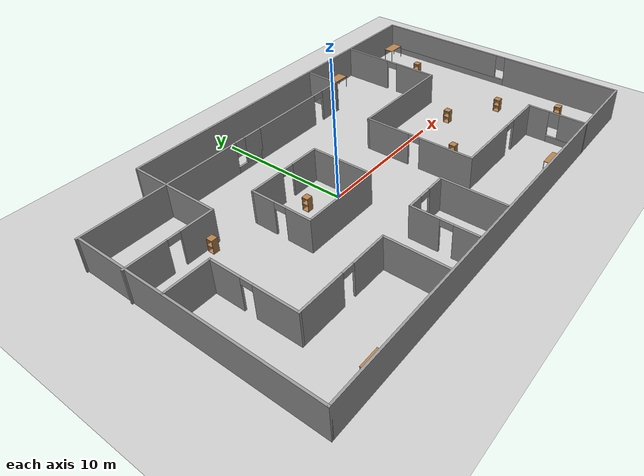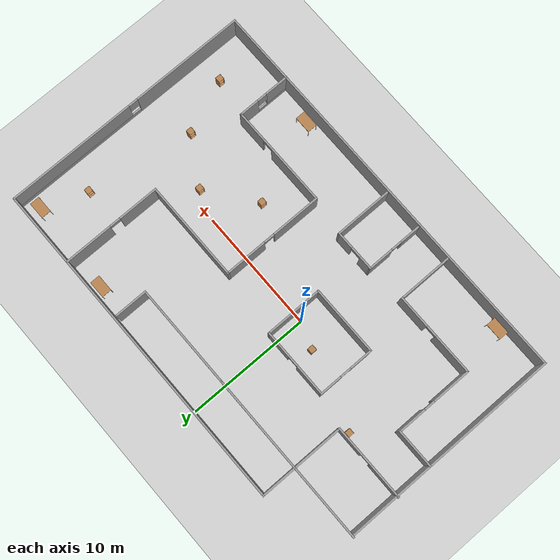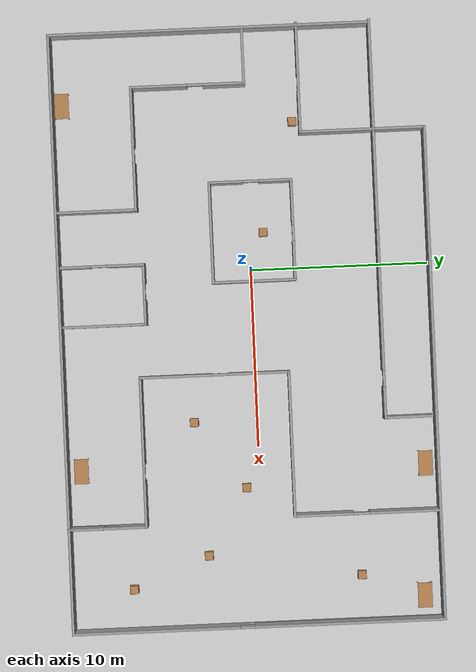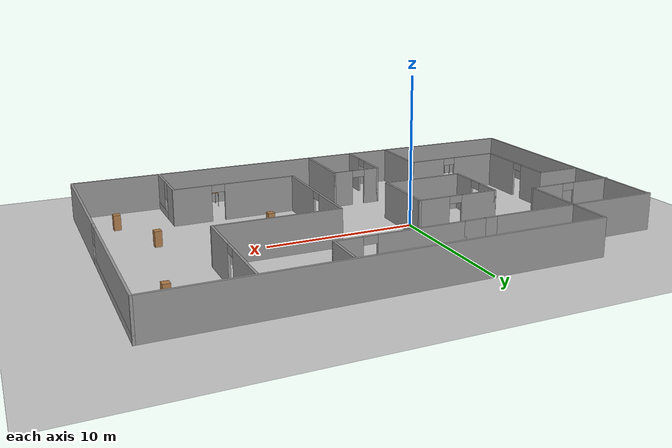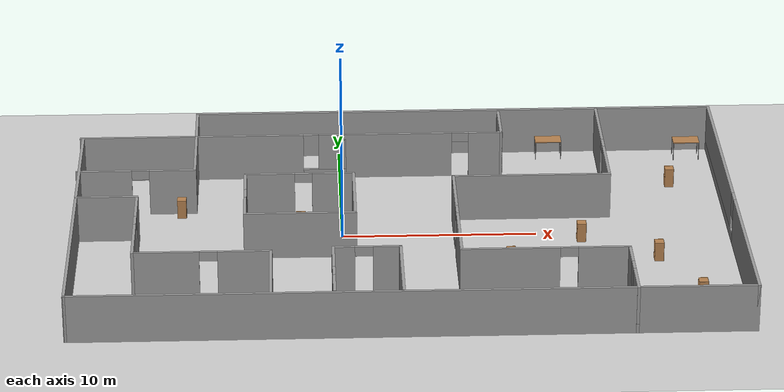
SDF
<sdf version="1.6">
 <world name="default">
  <light name="sun" type="directional">
   <pose>0 0 10 0 -0 0</pose>
   <diffuse>0.8 0.8 0.8 1</diffuse>
   <specular>0.1 0.1 0.1 1</specular>
   <attenuation>
    <range>1000</range>
    <constant>0.9</constant>
    <linear>0.01</linear>
    <quadratic>0.001</quadratic>
   </attenuation>
   <direction>-0.5 0.5 -1</direction>
  </light>
  <model name="ground_plane">
   <static>1</static>
   <link name="link">
    <collision name="collision">
     <geometry><plane><normal>0 0 1</normal><size>100 100</size></plane></geometry>
     <surface><friction><ode><mu>100</mu><mu2>50</mu2></ode></friction></surface>
    </collision>
    <visual name="visual">
     <cast_shadows>0</cast_shadows>
     <geometry><plane><normal>0 0 1</normal><size>100 100</size></plane></geometry>
     <material>
      <script><uri>file://media/materials/scripts/gazebo.material</uri><name>Gazebo/Grey</name></script>
     </material>
    </visual>
   </link>
  </model>
  <gravity>0 0 -9.8</gravity>
  <magnetic_field>6e-06 2.3e-05 -4.2e-05</magnetic_field>
  <atmosphere type="adiabatic"/>
  <physics name="default_physics" default="0" type="ode">
   <max_step_size>0.001</max_step_size>
   <real_time_factor>1</real_time_factor>
   <real_time_update_rate>1000</real_time_update_rate>
  </physics>
  <scene><ambient>0.4 0.4 0.4 1</ambient><background>0.7 0.7 0.7 1</background><shadows>1</shadows></scene>
  <spherical_coordinates>
   <surface_model>EARTH_WGS84</surface_model>
   <latitude_deg>0</latitude_deg>
   <longitude_deg>0</longitude_deg>
   <elevation>0</elevation>
   <heading_deg>0</heading_deg>
  </spherical_coordinates>
  <model name="myworld2.world">
   <pose>3.1644 -0.391877 0 0 -0 0</pose>
   <link name="Wall_11">
    <collision name="Wall_11_Collision">
     <geometry><box><size>18 0.15 2.5</size></box></geometry>
     <pose>0 0 1.25 0 -0 0</pose>
    </collision>
    <visual name="Wall_11_Visual">
     <pose>0 0 1.25 0 -0 0</pose>
     <geometry><box><size>18 0.15 2.5</size></box></geometry>
     <material>
      <script><uri>file://media/materials/scripts/gazebo.material</uri><name>Gazebo/Grey</name></script>
      <ambient>1 1 1 1</ambient>
     </material>
    </visual>
    <pose>-16.75 -1.4938 0 0 0 -1.5708</pose>
   </link>
   <link name="Wall_12">
    <collision name="Wall_12_Collision">
     <geometry><box><size>33.75 0.15 2.5</size></box></geometry>
     <pose>0 0 1.25 0 -0 0</pose>
    </collision>
    <visual name="Wall_12_Visual">
     <pose>0 0 1.25 0 -0 0</pose>
     <geometry><box><size>33.75 0.15 2.5</size></box></geometry>
     <material>
      <script><uri>file://media/materials/scripts/gazebo.material</uri><name>Gazebo/Grey</name></script>
      <ambient>1 1 1 1</ambient>
     </material>
    </visual>
    <pose>0.05 -10.4188 0 0 -0 0</pose>
   </link>
   <link name="Wall_13">
    <pose>16.85 0.006203 0 0 -0 1.5708</pose>
    <visual name="Wall_13_Visual_0">
     <pose>-5.77676 0 1.25 0 -0 0</pose>
     <geometry><box><size>9.44648 0.15 2.5</size></box></geometry>
     <material>
      <script><uri>file://media/materials/scripts/gazebo.material</uri><name>Gazebo/Grey</name></script>
      <ambient>1 1 1 1</ambient>
     </material>
    </visual>
    <collision name="Wall_13_Collision_0">
     <geometry><box><size>9.44648 0.15 2.5</size></box></geometry>
     <pose>-5.77676 0 1.25 0 -0 0</pose>
    </collision>
    <visual name="Wall_13_Visual_1">
     <pose>4.72324 0 0.25 0 -0 0</pose>
     <geometry><box><size>11.5535 0.15 0.5</size></box></geometry>
     <material>
      <script><uri>file://media/materials/scripts/gazebo.material</uri><name>Gazebo/Grey</name></script>
      <ambient>1 1 1 1</ambient>
     </material>
    </visual>
    <collision name="Wall_13_Collision_1">
     <geometry><box><size>11.5535 0.15 0.5</size></box></geometry>
     <pose>4.72324 0 0.25 0 -0 0</pose>
    </collision>
    <visual name="Wall_13_Visual_2">
     <pose>5.12324 0 1.5 0 -0 0</pose>
     <geometry><box><size>10.7535 0.15 2</size></box></geometry>
     <material>
      <script><uri>file://media/materials/scripts/gazebo.material</uri><name>Gazebo/Grey</name></script>
      <ambient>1 1 1 1</ambient>
     </material>
    </visual>
    <collision name="Wall_13_Collision_2">
     <geometry><box><size>10.7535 0.15 2</size></box></geometry>
     <pose>5.12324 0 1.5 0 -0 0</pose>
    </collision>
    <visual name="Wall_13_Visual_3">
     <pose>-0.653517 0 1.9 0 -0 0</pose>
     <geometry><box><size>0.8 0.15 1.2</size></box></geometry>
     <material>
      <script><uri>file://media/materials/scripts/gazebo.material</uri><name>Gazebo/Grey</name></script>
      <ambient>1 1 1 1</ambient>
     </material>
    </visual>
    <collision name="Wall_13_Collision_3">
     <geometry><box><size>0.8 0.15 1.2</size></box></geometry>
     <pose>-0.653517 0 1.9 0 -0 0</pose>
    </collision>
   </link>
   <link name="Wall_14">
    <collision name="Wall_14_Collision">
     <geometry><box><size>27.75 0.15 2.5</size></box></geometry>
     <pose>0 0 1.25 0 -0 0</pose>
    </collision>
    <visual name="Wall_14_Visual">
     <pose>0 0 1.25 0 -0 0</pose>
     <geometry><box><size>27.75 0.15 2.5</size></box></geometry>
     <material>
      <script><uri>file://media/materials/scripts/gazebo.material</uri><name>Gazebo/Grey</name></script>
      <ambient>1 1 1 1</ambient>
     </material>
    </visual>
    <pose>3.05 10.4312 0 0 -0 3.14159</pose>
   </link>
   <link name="Wall_15">
    <collision name="Wall_15_Collision">
     <geometry><box><size>3 0.15 2.5</size></box></geometry>
     <pose>0 0 1.25 0 -0 0</pose>
    </collision>
    <visual name="Wall_15_Visual">
     <pose>0 0 1.25 0 -0 0</pose>
     <geometry><box><size>3 0.15 2.5</size></box></geometry>
     <material>
      <script><uri>file://media/materials/scripts/gazebo.material</uri><name>Gazebo/Grey</name></script>
      <ambient>1 1 1 1</ambient>
     </material>
    </visual>
    <pose>-10.75 9.0062 0 0 0 -1.5708</pose>
   </link>
   <link name="Wall_18">
    <collision name="Wall_18_Collision">
     <geometry><box><size>6.25 0.15 2.5</size></box></geometry>
     <pose>0 0 1.25 0 -0 0</pose>
    </collision>
    <visual name="Wall_18_Visual">
     <pose>0 0 1.25 0 -0 0</pose>
     <geometry><box><size>6.25 0.15 2.5</size></box></geometry>
     <material>
      <script><uri>file://media/materials/scripts/gazebo.material</uri><name>Gazebo/Grey</name></script>
      <ambient>1 1 1 1</ambient>
     </material>
    </visual>
    <pose>-13.8 7.5812 0 0 -0 3.14159</pose>
   </link>
   <link name="Wall_20">
    <collision name="Wall_20_Collision">
     <geometry><box><size>4.25 0.15 2.5</size></box></geometry>
     <pose>0 0 1.25 0 -0 0</pose>
    </collision>
    <visual name="Wall_20_Visual">
     <pose>0 0 1.25 0 -0 0</pose>
     <geometry><box><size>4.25 0.15 2.5</size></box></geometry>
     <material>
      <script><uri>file://media/materials/scripts/gazebo.material</uri><name>Gazebo/Grey</name></script>
      <ambient>1 1 1 1</ambient>
     </material>
    </visual>
    <pose>-10.75 5.5312 0 0 0 -1.5708</pose>
   </link>
   <link name="Wall_22">
    <pose>-13.8 3.4812 0 0 -0 3.14159</pose>
    <visual name="Wall_22_Visual_0">
     <pose>-1.90313 0 1.25 0 -0 0</pose>
     <geometry><box><size>2.44374 0.15 2.5</size></box></geometry>
     <material>
      <script><uri>file://media/materials/scripts/gazebo.material</uri><name>Gazebo/Grey</name></script>
      <ambient>1 1 1 1</ambient>
     </material>
    </visual>
    <collision name="Wall_22_Collision_0">
     <geometry><box><size>2.44374 0.15 2.5</size></box></geometry>
     <pose>-1.90313 0 1.25 0 -0 0</pose>
    </collision>
    <visual name="Wall_22_Visual_1">
     <pose>1.67187 0 1.25 0 -0 0</pose>
     <geometry><box><size>2.90626 0.15 2.5</size></box></geometry>
     <material>
      <script><uri>file://media/materials/scripts/gazebo.material</uri><name>Gazebo/Grey</name></script>
      <ambient>1 1 1 1</ambient>
     </material>
    </visual>
    <collision name="Wall_22_Collision_1">
     <geometry><box><size>2.90626 0.15 2.5</size></box></geometry>
     <pose>1.67187 0 1.25 0 -0 0</pose>
    </collision>
    <visual name="Wall_22_Visual_2">
     <pose>-0.231259 0 2.25 0 -0 0</pose>
     <geometry><box><size>0.9 0.15 0.5</size></box></geometry>
     <material>
      <script><uri>file://media/materials/scripts/gazebo.material</uri><name>Gazebo/Grey</name></script>
      <ambient>1 1 1 1</ambient>
     </material>
    </visual>
    <collision name="Wall_22_Collision_2">
     <geometry><box><size>0.9 0.15 0.5</size></box></geometry>
     <pose>-0.231259 0 2.25 0 -0 0</pose>
    </collision>
   </link>
   <link name="Wall_24">
    <collision name="Wall_24_Collision">
     <geometry><box><size>3.25 0.15 2.5</size></box></geometry>
     <pose>0 0 1.25 0 -0 0</pose>
    </collision>
    <visual name="Wall_24_Visual">
     <pose>0 0 1.25 0 -0 0</pose>
     <geometry><box><size>3.25 0.15 2.5</size></box></geometry>
     <material>
      <script><uri>file://media/materials/scripts/gazebo.material</uri><name>Gazebo/Grey</name></script>
      <ambient>1 1 1 1</ambient>
     </material>
    </visual>
    <pose>-15.1851 0.43675 0 0 -0 0</pose>
   </link>
   <link name="Wall_25">
    <pose>-13.6351 -2.73825 0 0 0 -1.5708</pose>
    <visual name="Wall_25_Visual_0">
     <pose>-2.06306 0 1.25 0 -0 0</pose>
     <geometry><box><size>2.37387 0.15 2.5</size></box></geometry>
     <material>
      <script><uri>file://media/materials/scripts/gazebo.material</uri><name>Gazebo/Grey</name></script>
      <ambient>1 1 1 1</ambient>
     </material>
    </visual>
    <collision name="Wall_25_Collision_0">
     <geometry><box><size>2.37387 0.15 2.5</size></box></geometry>
     <pose>-2.06306 0 1.25 0 -0 0</pose>
    </collision>
    <visual name="Wall_25_Visual_1">
     <pose>1.63694 0 1.25 0 -0 0</pose>
     <geometry><box><size>3.22613 0.15 2.5</size></box></geometry>
     <material>
      <script><uri>file://media/materials/scripts/gazebo.material</uri><name>Gazebo/Grey</name></script>
      <ambient>1 1 1 1</ambient>
     </material>
    </visual>
    <collision name="Wall_25_Collision_1">
     <geometry><box><size>3.22613 0.15 2.5</size></box></geometry>
     <pose>1.63694 0 1.25 0 -0 0</pose>
    </collision>
    <visual name="Wall_25_Visual_2">
     <pose>-0.426125 0 2.25 0 -0 0</pose>
     <geometry><box><size>0.9 0.15 0.5</size></box></geometry>
     <material>
      <script><uri>file://media/materials/scripts/gazebo.material</uri><name>Gazebo/Grey</name></script>
      <ambient>1 1 1 1</ambient>
     </material>
    </visual>
    <collision name="Wall_25_Collision_2">
     <geometry><box><size>0.9 0.15 0.5</size></box></geometry>
     <pose>-0.426125 0 2.25 0 -0 0</pose>
    </collision>
   </link>
   <link name="Wall_26">
    <pose>-10.2101 -5.91325 0 0 -0 0</pose>
    <visual name="Wall_26_Visual_0">
     <pose>-1.80938 0 1.25 0 -0 0</pose>
     <geometry><box><size>3.38123 0.15 2.5</size></box></geometry>
     <material>
      <script><uri>file://media/materials/scripts/gazebo.material</uri><name>Gazebo/Grey</name></script>
      <ambient>1 1 1 1</ambient>
     </material>
    </visual>
    <collision name="Wall_26_Collision_0">
     <geometry><box><size>3.38123 0.15 2.5</size></box></geometry>
     <pose>-1.80938 0 1.25 0 -0 0</pose>
    </collision>
    <visual name="Wall_26_Visual_1">
     <pose>2.14062 0 1.25 0 -0 0</pose>
     <geometry><box><size>2.71877 0.15 2.5</size></box></geometry>
     <material>
      <script><uri>file://media/materials/scripts/gazebo.material</uri><name>Gazebo/Grey</name></script>
      <ambient>1 1 1 1</ambient>
     </material>
    </visual>
    <collision name="Wall_26_Collision_1">
     <geometry><box><size>2.71877 0.15 2.5</size></box></geometry>
     <pose>2.14062 0 1.25 0 -0 0</pose>
    </collision>
    <visual name="Wall_26_Visual_2">
     <pose>0.331232 0 2.25 0 -0 0</pose>
     <geometry><box><size>0.9 0.15 0.5</size></box></geometry>
     <material>
      <script><uri>file://media/materials/scripts/gazebo.material</uri><name>Gazebo/Grey</name></script>
      <ambient>1 1 1 1</ambient>
     </material>
    </visual>
    <collision name="Wall_26_Collision_2">
     <geometry><box><size>0.9 0.15 0.5</size></box></geometry>
     <pose>0.331232 0 2.25 0 -0 0</pose>
    </collision>
   </link>
   <link name="Wall_27">
    <collision name="Wall_27_Collision">
     <geometry><box><size>4.5 0.15 2.5</size></box></geometry>
     <pose>0 0 1.25 0 -0 0</pose>
    </collision>
    <visual name="Wall_27_Visual">
     <pose>0 0 1.25 0 -0 0</pose>
     <geometry><box><size>4.5 0.15 2.5</size></box></geometry>
     <material>
      <script><uri>file://media/materials/scripts/gazebo.material</uri><name>Gazebo/Grey</name></script>
      <ambient>1 1 1 1</ambient>
     </material>
    </visual>
    <pose>-6.78515 -8.08825 0 0 0 -1.5708</pose>
   </link>
   <link name="Wall_29">
    <pose>-8.11483 0.547824 0 0 0 -1.5708</pose>
    <visual name="Wall_29_Visual_0">
     <pose>-1.4379 0 1.25 0 -0 0</pose>
     <geometry><box><size>1.87421 0.15 2.5</size></box></geometry>
     <material>
      <script><uri>file://media/materials/scripts/gazebo.material</uri><name>Gazebo/Grey</name></script>
      <ambient>1 1 1 1</ambient>
     </material>
    </visual>
    <collision name="Wall_29_Collision_0">
     <geometry><box><size>1.87421 0.15 2.5</size></box></geometry>
     <pose>-1.4379 0 1.25 0 -0 0</pose>
    </collision>
    <visual name="Wall_29_Visual_1">
     <pose>1.3871 0 1.25 0 -0 0</pose>
     <geometry><box><size>1.97579 0.15 2.5</size></box></geometry>
     <material>
      <script><uri>file://media/materials/scripts/gazebo.material</uri><name>Gazebo/Grey</name></script>
      <ambient>1 1 1 1</ambient>
     </material>
    </visual>
    <collision name="Wall_29_Collision_1">
     <geometry><box><size>1.97579 0.15 2.5</size></box></geometry>
     <pose>1.3871 0 1.25 0 -0 0</pose>
    </collision>
    <visual name="Wall_29_Visual_2">
     <pose>-0.050792 0 2.25 0 -0 0</pose>
     <geometry><box><size>0.9 0.15 0.5</size></box></geometry>
     <material>
      <script><uri>file://media/materials/scripts/gazebo.material</uri><name>Gazebo/Grey</name></script>
      <ambient>1 1 1 1</ambient>
     </material>
    </visual>
    <collision name="Wall_29_Collision_2">
     <geometry><box><size>0.9 0.15 0.5</size></box></geometry>
     <pose>-0.050792 0 2.25 0 -0 0</pose>
    </collision>
   </link>
   <link name="Wall_30">
    <collision name="Wall_30_Collision">
     <geometry><box><size>5.75 0.15 2.5</size></box></geometry>
     <pose>0 0 1.25 0 -0 0</pose>
    </collision>
    <visual name="Wall_30_Visual">
     <pose>0 0 1.25 0 -0 0</pose>
     <geometry><box><size>5.75 0.15 2.5</size></box></geometry>
     <material>
      <script><uri>file://media/materials/scripts/gazebo.material</uri><name>Gazebo/Grey</name></script>
      <ambient>1 1 1 1</ambient>
     </material>
    </visual>
    <pose>-5.31483 -1.75218 0 0 -0 0</pose>
   </link>
   <link name="Wall_31">
    <collision name="Wall_31_Collision">
     <geometry><box><size>4.75 0.15 2.5</size></box></geometry>
     <pose>0 0 1.25 0 -0 0</pose>
    </collision>
    <visual name="Wall_31_Visual">
     <pose>0 0 1.25 0 -0 0</pose>
     <geometry><box><size>4.75 0.15 2.5</size></box></geometry>
     <material>
      <script><uri>file://media/materials/scripts/gazebo.material</uri><name>Gazebo/Grey</name></script>
      <ambient>1 1 1 1</ambient>
     </material>
    </visual>
    <pose>-2.51483 0.547824 0 0 -0 1.5708</pose>
   </link>
   <link name="Wall_32">
    <pose>-5.31483 2.84782 0 0 -0 3.14159</pose>
    <visual name="Wall_32_Visual_0">
     <pose>-1.76197 0 1.25 0 -0 0</pose>
     <geometry><box><size>2.22606 0.15 2.5</size></box></geometry>
     <material>
      <script><uri>file://media/materials/scripts/gazebo.material</uri><name>Gazebo/Grey</name></script>
      <ambient>1 1 1 1</ambient>
     </material>
    </visual>
    <collision name="Wall_32_Collision_0">
     <geometry><box><size>2.22606 0.15 2.5</size></box></geometry>
     <pose>-1.76197 0 1.25 0 -0 0</pose>
    </collision>
    <visual name="Wall_32_Visual_1">
     <pose>1.56303 0 1.25 0 -0 0</pose>
     <geometry><box><size>2.62394 0.15 2.5</size></box></geometry>
     <material>
      <script><uri>file://media/materials/scripts/gazebo.material</uri><name>Gazebo/Grey</name></script>
      <ambient>1 1 1 1</ambient>
     </material>
    </visual>
    <collision name="Wall_32_Collision_1">
     <geometry><box><size>2.62394 0.15 2.5</size></box></geometry>
     <pose>1.56303 0 1.25 0 -0 0</pose>
    </collision>
    <visual name="Wall_32_Visual_2">
     <pose>-0.198945 0 2.25 0 -0 0</pose>
     <geometry><box><size>0.9 0.15 0.5</size></box></geometry>
     <material>
      <script><uri>file://media/materials/scripts/gazebo.material</uri><name>Gazebo/Grey</name></script>
      <ambient>1 1 1 1</ambient>
     </material>
    </visual>
    <collision name="Wall_32_Collision_2">
     <geometry><box><size>0.9 0.15 0.5</size></box></geometry>
     <pose>-0.198945 0 2.25 0 -0 0</pose>
    </collision>
   </link>
   <link name="Wall_34">
    <pose>-6.825 7.5812 0 0 -0 0</pose>
    <visual name="Wall_34_Visual_0">
     <pose>-1.12533 0 1.25 0 -0 0</pose>
     <geometry><box><size>5.74934 0.15 2.5</size></box></geometry>
     <material>
      <script><uri>file://media/materials/scripts/gazebo.material</uri><name>Gazebo/Grey</name></script>
      <ambient>1 1 1 1</ambient>
     </material>
    </visual>
    <collision name="Wall_34_Collision_0">
     <geometry><box><size>5.74934 0.15 2.5</size></box></geometry>
     <pose>-1.12533 0 1.25 0 -0 0</pose>
    </collision>
    <visual name="Wall_34_Visual_1">
     <pose>2.87467 0 0.25 0 -0 0</pose>
     <geometry><box><size>2.25066 0.15 0.5</size></box></geometry>
     <material>
      <script><uri>file://media/materials/scripts/gazebo.material</uri><name>Gazebo/Grey</name></script>
      <ambient>1 1 1 1</ambient>
     </material>
    </visual>
    <collision name="Wall_34_Collision_1">
     <geometry><box><size>2.25066 0.15 0.5</size></box></geometry>
     <pose>2.87467 0 0.25 0 -0 0</pose>
    </collision>
    <visual name="Wall_34_Visual_2">
     <pose>3.27467 0 1.5 0 -0 0</pose>
     <geometry><box><size>1.45066 0.15 2</size></box></geometry>
     <material>
      <script><uri>file://media/materials/scripts/gazebo.material</uri><name>Gazebo/Grey</name></script>
      <ambient>1 1 1 1</ambient>
     </material>
    </visual>
    <collision name="Wall_34_Collision_2">
     <geometry><box><size>1.45066 0.15 2</size></box></geometry>
     <pose>3.27467 0 1.5 0 -0 0</pose>
    </collision>
    <visual name="Wall_34_Visual_3">
     <pose>2.14934 0 1.9 0 -0 0</pose>
     <geometry><box><size>0.8 0.15 1.2</size></box></geometry>
     <material>
      <script><uri>file://media/materials/scripts/gazebo.material</uri><name>Gazebo/Grey</name></script>
      <ambient>1 1 1 1</ambient>
     </material>
    </visual>
    <collision name="Wall_34_Collision_3">
     <geometry><box><size>0.8 0.15 1.2</size></box></geometry>
     <pose>2.14934 0 1.9 0 -0 0</pose>
    </collision>
   </link>
   <link name="Wall_35">
    <pose>1.275 7.5812 0 0 -0 0</pose>
    <visual name="Wall_35_Visual_0">
     <pose>-1.35831 0 1.25 0 -0 0</pose>
     <geometry><box><size>5.78337 0.15 2.5</size></box></geometry>
     <material>
      <script><uri>file://media/materials/scripts/gazebo.material</uri><name>Gazebo/Grey</name></script>
      <ambient>1 1 1 1</ambient>
     </material>
    </visual>
    <collision name="Wall_35_Collision_0">
     <geometry><box><size>5.78337 0.15 2.5</size></box></geometry>
     <pose>-1.35831 0 1.25 0 -0 0</pose>
    </collision>
    <visual name="Wall_35_Visual_1">
     <pose>3.34169 0 1.25 0 -0 0</pose>
     <geometry><box><size>1.81663 0.15 2.5</size></box></geometry>
     <material>
      <script><uri>file://media/materials/scripts/gazebo.material</uri><name>Gazebo/Grey</name></script>
      <ambient>1 1 1 1</ambient>
     </material>
    </visual>
    <collision name="Wall_35_Collision_1">
     <geometry><box><size>1.81663 0.15 2.5</size></box></geometry>
     <pose>3.34169 0 1.25 0 -0 0</pose>
    </collision>
    <visual name="Wall_35_Visual_2">
     <pose>1.98337 0 2.25 0 -0 0</pose>
     <geometry><box><size>0.9 0.15 0.5</size></box></geometry>
     <material>
      <script><uri>file://media/materials/scripts/gazebo.material</uri><name>Gazebo/Grey</name></script>
      <ambient>1 1 1 1</ambient>
     </material>
    </visual>
    <collision name="Wall_35_Collision_2">
     <geometry><box><size>0.9 0.15 0.5</size></box></geometry>
     <pose>1.98337 0 2.25 0 -0 0</pose>
    </collision>
   </link>
   <link name="Wall_36">
    <collision name="Wall_36_Collision">
     <geometry><box><size>2.75 0.15 2.5</size></box></geometry>
     <pose>0 0 1.25 0 -0 0</pose>
    </collision>
    <visual name="Wall_36_Visual">
     <pose>0 0 1.25 0 -0 0</pose>
     <geometry><box><size>2.75 0.15 2.5</size></box></geometry>
     <material>
      <script><uri>file://media/materials/scripts/gazebo.material</uri><name>Gazebo/Grey</name></script>
      <ambient>1 1 1 1</ambient>
     </material>
    </visual>
    <pose>5.45 8.8812 0 0 -0 1.5708</pose>
   </link>
   <link name="Wall_38">
    <pose>10.7452 6.3188 0 0 0 -1.5708</pose>
    <visual name="Wall_38_Visual_0">
     <pose>-2.14476 0 1.25 0 -0 0</pose>
     <geometry><box><size>3.96048 0.15 2.5</size></box></geometry>
     <material>
      <script><uri>file://media/materials/scripts/gazebo.material</uri><name>Gazebo/Grey</name></script>
      <ambient>1 1 1 1</ambient>
     </material>
    </visual>
    <collision name="Wall_38_Collision_0">
     <geometry><box><size>3.96048 0.15 2.5</size></box></geometry>
     <pose>-2.14476 0 1.25 0 -0 0</pose>
    </collision>
    <visual name="Wall_38_Visual_1">
     <pose>2.43024 0 1.25 0 -0 0</pose>
     <geometry><box><size>3.38952 0.15 2.5</size></box></geometry>
     <material>
      <script><uri>file://media/materials/scripts/gazebo.material</uri><name>Gazebo/Grey</name></script>
      <ambient>1 1 1 1</ambient>
     </material>
    </visual>
    <collision name="Wall_38_Collision_1">
     <geometry><box><size>3.38952 0.15 2.5</size></box></geometry>
     <pose>2.43024 0 1.25 0 -0 0</pose>
    </collision>
    <visual name="Wall_38_Visual_2">
     <pose>0.285484 0 2.25 0 -0 0</pose>
     <geometry><box><size>0.9 0.15 0.5</size></box></geometry>
     <material>
      <script><uri>file://media/materials/scripts/gazebo.material</uri><name>Gazebo/Grey</name></script>
      <ambient>1 1 1 1</ambient>
     </material>
    </visual>
    <collision name="Wall_38_Collision_2">
     <geometry><box><size>0.9 0.15 0.5</size></box></geometry>
     <pose>0.285484 0 2.25 0 -0 0</pose>
    </collision>
   </link>
   <link name="Wall_39">
    <collision name="Wall_39_Collision">
     <geometry><box><size>8.25 0.15 2.5</size></box></geometry>
     <pose>0 0 1.25 0 -0 0</pose>
    </collision>
    <visual name="Wall_39_Visual">
     <pose>0 0 1.25 0 -0 0</pose>
     <geometry><box><size>8.25 0.15 2.5</size></box></geometry>
     <material>
      <script><uri>file://media/materials/scripts/gazebo.material</uri><name>Gazebo/Grey</name></script>
      <ambient>1 1 1 1</ambient>
     </material>
    </visual>
    <pose>6.69523 2.2688 0 0 -0 3.14159</pose>
   </link>
   <link name="Wall_40">
    <pose>2.64523 -1.9062 0 0 0 -1.5708</pose>
    <visual name="Wall_40_Visual_0">
     <pose>-2.5013 0 1.25 0 -0 0</pose>
     <geometry><box><size>3.49741 0.15 2.5</size></box></geometry>
     <material>
      <script><uri>file://media/materials/scripts/gazebo.material</uri><name>Gazebo/Grey</name></script>
      <ambient>1 1 1 1</ambient>
     </material>
    </visual>
    <collision name="Wall_40_Collision_0">
     <geometry><box><size>3.49741 0.15 2.5</size></box></geometry>
     <pose>-2.5013 0 1.25 0 -0 0</pose>
    </collision>
    <visual name="Wall_40_Visual_1">
     <pose>2.1987 0 1.25 0 -0 0</pose>
     <geometry><box><size>4.10259 0.15 2.5</size></box></geometry>
     <material>
      <script><uri>file://media/materials/scripts/gazebo.material</uri><name>Gazebo/Grey</name></script>
      <ambient>1 1 1 1</ambient>
     </material>
    </visual>
    <collision name="Wall_40_Collision_1">
     <geometry><box><size>4.10259 0.15 2.5</size></box></geometry>
     <pose>2.1987 0 1.25 0 -0 0</pose>
    </collision>
    <visual name="Wall_40_Visual_2">
     <pose>-0.302592 0 2.25 0 -0 0</pose>
     <geometry><box><size>0.9 0.15 0.5</size></box></geometry>
     <material>
      <script><uri>file://media/materials/scripts/gazebo.material</uri><name>Gazebo/Grey</name></script>
      <ambient>1 1 1 1</ambient>
     </material>
    </visual>
    <collision name="Wall_40_Collision_2">
     <geometry><box><size>0.9 0.15 0.5</size></box></geometry>
     <pose>-0.302592 0 2.25 0 -0 0</pose>
    </collision>
   </link>
   <link name="Wall_41">
    <pose>6.82023 -6.0812 0 0 -0 0</pose>
    <visual name="Wall_41_Visual_0">
     <pose>-1.76501 0 1.25 0 -0 0</pose>
     <geometry><box><size>4.96999 0.15 2.5</size></box></geometry>
     <material>
      <script><uri>file://media/materials/scripts/gazebo.material</uri><name>Gazebo/Grey</name></script>
      <ambient>1 1 1 1</ambient>
     </material>
    </visual>
    <collision name="Wall_41_Collision_0">
     <geometry><box><size>4.96999 0.15 2.5</size></box></geometry>
     <pose>-1.76501 0 1.25 0 -0 0</pose>
    </collision>
    <visual name="Wall_41_Visual_1">
     <pose>2.93499 0 1.25 0 -0 0</pose>
     <geometry><box><size>2.63001 0.15 2.5</size></box></geometry>
     <material>
      <script><uri>file://media/materials/scripts/gazebo.material</uri><name>Gazebo/Grey</name></script>
      <ambient>1 1 1 1</ambient>
     </material>
    </visual>
    <collision name="Wall_41_Collision_1">
     <geometry><box><size>2.63001 0.15 2.5</size></box></geometry>
     <pose>2.93499 0 1.25 0 -0 0</pose>
    </collision>
    <visual name="Wall_41_Visual_2">
     <pose>1.16999 0 2.25 0 -0 0</pose>
     <geometry><box><size>0.9 0.15 0.5</size></box></geometry>
     <material>
      <script><uri>file://media/materials/scripts/gazebo.material</uri><name>Gazebo/Grey</name></script>
      <ambient>1 1 1 1</ambient>
     </material>
    </visual>
    <collision name="Wall_41_Collision_2">
     <geometry><box><size>0.9 0.15 0.5</size></box></geometry>
     <pose>1.16999 0 2.25 0 -0 0</pose>
    </collision>
   </link>
   <link name="Wall_42">
    <pose>10.9952 -8.2562 0 0 0 -1.5708</pose>
    <visual name="Wall_42_Visual_0">
     <pose>-1.41232 0 1.25 0 -0 0</pose>
     <geometry><box><size>1.67535 0.15 2.5</size></box></geometry>
     <material>
      <script><uri>file://media/materials/scripts/gazebo.material</uri><name>Gazebo/Grey</name></script>
      <ambient>1 1 1 1</ambient>
     </material>
    </visual>
    <collision name="Wall_42_Collision_0">
     <geometry><box><size>1.67535 0.15 2.5</size></box></geometry>
     <pose>-1.41232 0 1.25 0 -0 0</pose>
    </collision>
    <visual name="Wall_42_Visual_1">
     <pose>0.837676 0 0.25 0 -0 0</pose>
     <geometry><box><size>2.82465 0.15 0.5</size></box></geometry>
     <material>
      <script><uri>file://media/materials/scripts/gazebo.material</uri><name>Gazebo/Grey</name></script>
      <ambient>1 1 1 1</ambient>
     </material>
    </visual>
    <collision name="Wall_42_Collision_1">
     <geometry><box><size>2.82465 0.15 0.5</size></box></geometry>
     <pose>0.837676 0 0.25 0 -0 0</pose>
    </collision>
    <visual name="Wall_42_Visual_2">
     <pose>1.23768 0 1.5 0 -0 0</pose>
     <geometry><box><size>2.02465 0.15 2</size></box></geometry>
     <material>
      <script><uri>file://media/materials/scripts/gazebo.material</uri><name>Gazebo/Grey</name></script>
      <ambient>1 1 1 1</ambient>
     </material>
    </visual>
    <collision name="Wall_42_Collision_2">
     <geometry><box><size>2.02465 0.15 2</size></box></geometry>
     <pose>1.23768 0 1.5 0 -0 0</pose>
    </collision>
    <visual name="Wall_42_Visual_3">
     <pose>-0.174648 0 1.9 0 -0 0</pose>
     <geometry><box><size>0.8 0.15 1.2</size></box></geometry>
     <material>
      <script><uri>file://media/materials/scripts/gazebo.material</uri><name>Gazebo/Grey</name></script>
      <ambient>1 1 1 1</ambient>
     </material>
    </visual>
    <collision name="Wall_42_Collision_3">
     <geometry><box><size>0.8 0.15 1.2</size></box></geometry>
     <pose>-0.174648 0 1.9 0 -0 0</pose>
    </collision>
   </link>
   <link name="Wall_45">
    <pose>-3.70242 -7.93505 0 0 -0 1.5708</pose>
    <visual name="Wall_45_Visual_0">
     <pose>-1.51883 0 1.25 0 -0 0</pose>
     <geometry><box><size>1.71234 0.15 2.5</size></box></geometry>
     <material>
      <script><uri>file://media/materials/scripts/gazebo.material</uri><name>Gazebo/Grey</name></script>
      <ambient>1 1 1 1</ambient>
     </material>
    </visual>
    <collision name="Wall_45_Collision_0">
     <geometry><box><size>1.71234 0.15 2.5</size></box></geometry>
     <pose>-1.51883 0 1.25 0 -0 0</pose>
    </collision>
    <visual name="Wall_45_Visual_1">
     <pose>1.30617 0 1.25 0 -0 0</pose>
     <geometry><box><size>2.13766 0.15 2.5</size></box></geometry>
     <material>
      <script><uri>file://media/materials/scripts/gazebo.material</uri><name>Gazebo/Grey</name></script>
      <ambient>1 1 1 1</ambient>
     </material>
    </visual>
    <collision name="Wall_45_Collision_1">
     <geometry><box><size>2.13766 0.15 2.5</size></box></geometry>
     <pose>1.30617 0 1.25 0 -0 0</pose>
    </collision>
    <visual name="Wall_45_Visual_2">
     <pose>-0.21266 0 2.25 0 -0 0</pose>
     <geometry><box><size>0.9 0.15 0.5</size></box></geometry>
     <material>
      <script><uri>file://media/materials/scripts/gazebo.material</uri><name>Gazebo/Grey</name></script>
      <ambient>1 1 1 1</ambient>
     </material>
    </visual>
    <collision name="Wall_45_Collision_2">
     <geometry><box><size>0.9 0.15 0.5</size></box></geometry>
     <pose>-0.21266 0 2.25 0 -0 0</pose>
    </collision>
   </link>
   <link name="Wall_46">
    <pose>-2.02743 -5.63505 0 0 -0 0</pose>
    <visual name="Wall_46_Visual_0">
     <pose>-1.1759 0 1.25 0 -0 0</pose>
     <geometry><box><size>1.14819 0.15 2.5</size></box></geometry>
     <material>
      <script><uri>file://media/materials/scripts/gazebo.material</uri><name>Gazebo/Grey</name></script>
      <ambient>1 1 1 1</ambient>
     </material>
    </visual>
    <collision name="Wall_46_Collision_0">
     <geometry><box><size>1.14819 0.15 2.5</size></box></geometry>
     <pose>-1.1759 0 1.25 0 -0 0</pose>
    </collision>
    <visual name="Wall_46_Visual_1">
     <pose>1.0241 0 1.25 0 -0 0</pose>
     <geometry><box><size>1.45181 0.15 2.5</size></box></geometry>
     <material>
      <script><uri>file://media/materials/scripts/gazebo.material</uri><name>Gazebo/Grey</name></script>
      <ambient>1 1 1 1</ambient>
     </material>
    </visual>
    <collision name="Wall_46_Collision_1">
     <geometry><box><size>1.45181 0.15 2.5</size></box></geometry>
     <pose>1.0241 0 1.25 0 -0 0</pose>
    </collision>
    <visual name="Wall_46_Visual_2">
     <pose>-0.151806 0 2.25 0 -0 0</pose>
     <geometry><box><size>0.9 0.15 0.5</size></box></geometry>
     <material>
      <script><uri>file://media/materials/scripts/gazebo.material</uri><name>Gazebo/Grey</name></script>
      <ambient>1 1 1 1</ambient>
     </material>
    </visual>
    <collision name="Wall_46_Collision_2">
     <geometry><box><size>0.9 0.15 0.5</size></box></geometry>
     <pose>-0.151806 0 2.25 0 -0 0</pose>
    </collision>
   </link>
   <link name="Wall_47">
    <collision name="Wall_47_Collision">
     <geometry><box><size>4.75 0.15 2.5</size></box></geometry>
     <pose>0 0 1.25 0 -0 0</pose>
    </collision>
    <visual name="Wall_47_Visual">
     <pose>0 0 1.25 0 -0 0</pose>
     <geometry><box><size>4.75 0.15 2.5</size></box></geometry>
     <material>
      <script><uri>file://media/materials/scripts/gazebo.material</uri><name>Gazebo/Grey</name></script>
      <ambient>1 1 1 1</ambient>
     </material>
    </visual>
    <pose>-0.352425 -7.93505 0 0 0 -1.5708</pose>
   </link>
   <static>1</static>
  </model>
  <model name="cabinet">
   <static>1</static>
   <link name="cabinet_bottom_plate">
    <inertial>
     <pose>0 0 -1 0 -0 0</pose>
     <inertia><ixx>2.05</ixx><ixy>0</ixy><ixz>0</ixz><iyy>2.05</iyy><iyz>0</iyz><izz>2.05</izz></inertia>
     <mass>25</mass>
    </inertial>
    <collision name="cabinet_bottom_plate_geom">
     <pose>0 0 0.01 0 -0 0</pose>
     <geometry><box><size>0.45 0.45 0.02</size></box></geometry>
    </collision>
    <visual name="cabinet_bottom_plate_geom_visual">
     <pose>0 0 0.01 0 -0 0</pose>
     <geometry><box><size>0.45 0.45 0.02</size></box></geometry>
     <material>
      <script><uri>file://media/materials/scripts/gazebo.material</uri><name>Gazebo/Wood</name></script>
     </material>
    </visual>
    <collision name="cabinet_bottom_plate_geom_cabinet_back_plate">
     <pose>0.235 0 0.51 0 -0 0</pose>
     <geometry><box><size>0.02 0.45 1.02</size></box></geometry>
    </collision>
    <visual name="cabinet_bottom_plate_geom_cabinet_back_plate_visual">
     <pose>0.235 0 0.51 0 -0 0</pose>
     <geometry><box><size>0.02 0.45 1.02</size></box></geometry>
     <material>
      <script><uri>file://media/materials/scripts/gazebo.material</uri><name>Gazebo/Wood</name></script>
     </material>
    </visual>
    <collision name="cabinet_bottom_plate_geom_cabinet_left_plate">
     <pose>0 0.235 0.51 0 -0 0</pose>
     <geometry><box><size>0.45 0.02 1.02</size></box></geometry>
    </collision>
    <visual name="cabinet_bottom_plate_geom_cabinet_left_plate_visual">
     <pose>0 0.235 0.51 0 -0 0</pose>
     <geometry><box><size>0.45 0.02 1.02</size></box></geometry>
     <material>
      <script><uri>file://media/materials/scripts/gazebo.material</uri><name>Gazebo/Wood</name></script>
     </material>
    </visual>
    <collision name="cabinet_bottom_plate_geom_cabinet_middle_plate">
     <pose>0 0 0.51 0 -0 0</pose>
     <geometry><box><size>0.45 0.45 0.02</size></box></geometry>
    </collision>
    <visual name="cabinet_bottom_plate_geom_cabinet_middle_plate_visual">
     <pose>0 0 0.51 0 -0 0</pose>
     <geometry><box><size>0.45 0.45 0.02</size></box></geometry>
     <material>
      <script><uri>file://media/materials/scripts/gazebo.material</uri><name>Gazebo/Wood</name></script>
     </material>
    </visual>
    <collision name="cabinet_bottom_plate_geom_cabinet_right_plate">
     <pose>0 -0.235 0.51 0 -0 0</pose>
     <geometry><box><size>0.45 0.02 1.02</size></box></geometry>
    </collision>
    <visual name="cabinet_bottom_plate_geom_cabinet_right_plate_visual">
     <pose>0 -0.235 0.51 0 -0 0</pose>
     <geometry><box><size>0.45 0.02 1.02</size></box></geometry>
     <material>
      <script><uri>file://media/materials/scripts/gazebo.material</uri><name>Gazebo/Wood</name></script>
     </material>
    </visual>
    <collision name="cabinet_bottom_plate_geom_cabinet_top_plate">
     <pose>0 0 1.01 0 -0 0</pose>
     <geometry><box><size>0.45 0.45 0.02</size></box></geometry>
    </collision>
    <visual name="cabinet_bottom_plate_geom_cabinet_top_plate_visual">
     <pose>0 0 1.01 0 -0 0</pose>
     <geometry><box><size>0.45 0.45 0.02</size></box></geometry>
     <material>
      <script><uri>file://media/materials/scripts/gazebo.material</uri><name>Gazebo/Wood</name></script>
     </material>
    </visual>
   </link>
   <pose>-8.29466 2.67213 0 0 -0 0</pose>
  </model>
  <model name="cabinet_0">
   <static>1</static>
   <link name="cabinet_bottom_plate">
    <inertial>
     <pose>0 0 -1 0 -0 0</pose>
     <inertia><ixx>2.05</ixx><ixy>0</ixy><ixz>0</ixz><iyy>2.05</iyy><iyz>0</iyz><izz>2.05</izz></inertia>
     <mass>25</mass>
    </inertial>
    <collision name="cabinet_bottom_plate_geom">
     <pose>0 0 0.01 0 -0 0</pose>
     <geometry><box><size>0.45 0.45 0.02</size></box></geometry>
    </collision>
    <visual name="cabinet_bottom_plate_geom_visual">
     <pose>0 0 0.01 0 -0 0</pose>
     <geometry><box><size>0.45 0.45 0.02</size></box></geometry>
     <material>
      <script><uri>file://media/materials/scripts/gazebo.material</uri><name>Gazebo/Wood</name></script>
     </material>
    </visual>
    <collision name="cabinet_bottom_plate_geom_cabinet_back_plate">
     <pose>0.235 0 0.51 0 -0 0</pose>
     <geometry><box><size>0.02 0.45 1.02</size></box></geometry>
    </collision>
    <visual name="cabinet_bottom_plate_geom_cabinet_back_plate_visual">
     <pose>0.235 0 0.51 0 -0 0</pose>
     <geometry><box><size>0.02 0.45 1.02</size></box></geometry>
     <material>
      <script><uri>file://media/materials/scripts/gazebo.material</uri><name>Gazebo/Wood</name></script>
     </material>
    </visual>
    <collision name="cabinet_bottom_plate_geom_cabinet_left_plate">
     <pose>0 0.235 0.51 0 -0 0</pose>
     <geometry><box><size>0.45 0.02 1.02</size></box></geometry>
    </collision>
    <visual name="cabinet_bottom_plate_geom_cabinet_left_plate_visual">
     <pose>0 0.235 0.51 0 -0 0</pose>
     <geometry><box><size>0.45 0.02 1.02</size></box></geometry>
     <material>
      <script><uri>file://media/materials/scripts/gazebo.material</uri><name>Gazebo/Wood</name></script>
     </material>
    </visual>
    <collision name="cabinet_bottom_plate_geom_cabinet_middle_plate">
     <pose>0 0 0.51 0 -0 0</pose>
     <geometry><box><size>0.45 0.45 0.02</size></box></geometry>
    </collision>
    <visual name="cabinet_bottom_plate_geom_cabinet_middle_plate_visual">
     <pose>0 0 0.51 0 -0 0</pose>
     <geometry><box><size>0.45 0.45 0.02</size></box></geometry>
     <material>
      <script><uri>file://media/materials/scripts/gazebo.material</uri><name>Gazebo/Wood</name></script>
     </material>
    </visual>
    <collision name="cabinet_bottom_plate_geom_cabinet_right_plate">
     <pose>0 -0.235 0.51 0 -0 0</pose>
     <geometry><box><size>0.45 0.02 1.02</size></box></geometry>
    </collision>
    <visual name="cabinet_bottom_plate_geom_cabinet_right_plate_visual">
     <pose>0 -0.235 0.51 0 -0 0</pose>
     <geometry><box><size>0.45 0.02 1.02</size></box></geometry>
     <material>
      <script><uri>file://media/materials/scripts/gazebo.material</uri><name>Gazebo/Wood</name></script>
     </material>
    </visual>
    <collision name="cabinet_bottom_plate_geom_cabinet_top_plate">
     <pose>0 0 1.01 0 -0 0</pose>
     <geometry><box><size>0.45 0.45 0.02</size></box></geometry>
    </collision>
    <visual name="cabinet_bottom_plate_geom_cabinet_top_plate_visual">
     <pose>0 0 1.01 0 -0 0</pose>
     <geometry><box><size>0.45 0.45 0.02</size></box></geometry>
     <material>
      <script><uri>file://media/materials/scripts/gazebo.material</uri><name>Gazebo/Wood</name></script>
     </material>
    </visual>
   </link>
   <pose>-2.11277 0.776709 0 0 -0 0</pose>
  </model>
  <model name="cabinet_1">
   <static>1</static>
   <link name="cabinet_bottom_plate">
    <inertial>
     <pose>0 0 -1 0 -0 0</pose>
     <inertia><ixx>2.05</ixx><ixy>0</ixy><ixz>0</ixz><iyy>2.05</iyy><iyz>0</iyz><izz>2.05</izz></inertia>
     <mass>25</mass>
    </inertial>
    <collision name="cabinet_bottom_plate_geom">
     <pose>0 0 0.01 0 -0 0</pose>
     <geometry><box><size>0.45 0.45 0.02</size></box></geometry>
    </collision>
    <visual name="cabinet_bottom_plate_geom_visual">
     <pose>0 0 0.01 0 -0 0</pose>
     <geometry><box><size>0.45 0.45 0.02</size></box></geometry>
     <material>
      <script><uri>file://media/materials/scripts/gazebo.material</uri><name>Gazebo/Wood</name></script>
     </material>
    </visual>
    <collision name="cabinet_bottom_plate_geom_cabinet_back_plate">
     <pose>0.235 0 0.51 0 -0 0</pose>
     <geometry><box><size>0.02 0.45 1.02</size></box></geometry>
    </collision>
    <visual name="cabinet_bottom_plate_geom_cabinet_back_plate_visual">
     <pose>0.235 0 0.51 0 -0 0</pose>
     <geometry><box><size>0.02 0.45 1.02</size></box></geometry>
     <material>
      <script><uri>file://media/materials/scripts/gazebo.material</uri><name>Gazebo/Wood</name></script>
     </material>
    </visual>
    <collision name="cabinet_bottom_plate_geom_cabinet_left_plate">
     <pose>0 0.235 0.51 0 -0 0</pose>
     <geometry><box><size>0.45 0.02 1.02</size></box></geometry>
    </collision>
    <visual name="cabinet_bottom_plate_geom_cabinet_left_plate_visual">
     <pose>0 0.235 0.51 0 -0 0</pose>
     <geometry><box><size>0.45 0.02 1.02</size></box></geometry>
     <material>
      <script><uri>file://media/materials/scripts/gazebo.material</uri><name>Gazebo/Wood</name></script>
     </material>
    </visual>
    <collision name="cabinet_bottom_plate_geom_cabinet_middle_plate">
     <pose>0 0 0.51 0 -0 0</pose>
     <geometry><box><size>0.45 0.45 0.02</size></box></geometry>
    </collision>
    <visual name="cabinet_bottom_plate_geom_cabinet_middle_plate_visual">
     <pose>0 0 0.51 0 -0 0</pose>
     <geometry><box><size>0.45 0.45 0.02</size></box></geometry>
     <material>
      <script><uri>file://media/materials/scripts/gazebo.material</uri><name>Gazebo/Wood</name></script>
     </material>
    </visual>
    <collision name="cabinet_bottom_plate_geom_cabinet_right_plate">
     <pose>0 -0.235 0.51 0 -0 0</pose>
     <geometry><box><size>0.45 0.02 1.02</size></box></geometry>
    </collision>
    <visual name="cabinet_bottom_plate_geom_cabinet_right_plate_visual">
     <pose>0 -0.235 0.51 0 -0 0</pose>
     <geometry><box><size>0.45 0.02 1.02</size></box></geometry>
     <material>
      <script><uri>file://media/materials/scripts/gazebo.material</uri><name>Gazebo/Wood</name></script>
     </material>
    </visual>
    <collision name="cabinet_bottom_plate_geom_cabinet_top_plate">
     <pose>0 0 1.01 0 -0 0</pose>
     <geometry><box><size>0.45 0.45 0.02</size></box></geometry>
    </collision>
    <visual name="cabinet_bottom_plate_geom_cabinet_top_plate_visual">
     <pose>0 0 1.01 0 -0 0</pose>
     <geometry><box><size>0.45 0.45 0.02</size></box></geometry>
     <material>
      <script><uri>file://media/materials/scripts/gazebo.material</uri><name>Gazebo/Wood</name></script>
     </material>
    </visual>
   </link>
   <pose>12.2686 -0.764283 0 0 -0 0</pose>
  </model>
  <model name="cabinet_2">
   <static>1</static>
   <link name="cabinet_bottom_plate">
    <inertial>
     <pose>0 0 -1 0 -0 0</pose>
     <inertia><ixx>2.05</ixx><ixy>0</ixy><ixz>0</ixz><iyy>2.05</iyy><iyz>0</iyz><izz>2.05</izz></inertia>
     <mass>25</mass>
    </inertial>
    <collision name="cabinet_bottom_plate_geom">
     <pose>0 0 0.01 0 -0 0</pose>
     <geometry><box><size>0.45 0.45 0.02</size></box></geometry>
    </collision>
    <visual name="cabinet_bottom_plate_geom_visual">
     <pose>0 0 0.01 0 -0 0</pose>
     <geometry><box><size>0.45 0.45 0.02</size></box></geometry>
     <material>
      <script><uri>file://media/materials/scripts/gazebo.material</uri><name>Gazebo/Wood</name></script>
     </material>
    </visual>
    <collision name="cabinet_bottom_plate_geom_cabinet_back_plate">
     <pose>0.235 0 0.51 0 -0 0</pose>
     <geometry><box><size>0.02 0.45 1.02</size></box></geometry>
    </collision>
    <visual name="cabinet_bottom_plate_geom_cabinet_back_plate_visual">
     <pose>0.235 0 0.51 0 -0 0</pose>
     <geometry><box><size>0.02 0.45 1.02</size></box></geometry>
     <material>
      <script><uri>file://media/materials/scripts/gazebo.material</uri><name>Gazebo/Wood</name></script>
     </material>
    </visual>
    <collision name="cabinet_bottom_plate_geom_cabinet_left_plate">
     <pose>0 0.235 0.51 0 -0 0</pose>
     <geometry><box><size>0.45 0.02 1.02</size></box></geometry>
    </collision>
    <visual name="cabinet_bottom_plate_geom_cabinet_left_plate_visual">
     <pose>0 0.235 0.51 0 -0 0</pose>
     <geometry><box><size>0.45 0.02 1.02</size></box></geometry>
     <material>
      <script><uri>file://media/materials/scripts/gazebo.material</uri><name>Gazebo/Wood</name></script>
     </material>
    </visual>
    <collision name="cabinet_bottom_plate_geom_cabinet_middle_plate">
     <pose>0 0 0.51 0 -0 0</pose>
     <geometry><box><size>0.45 0.45 0.02</size></box></geometry>
    </collision>
    <visual name="cabinet_bottom_plate_geom_cabinet_middle_plate_visual">
     <pose>0 0 0.51 0 -0 0</pose>
     <geometry><box><size>0.45 0.45 0.02</size></box></geometry>
     <material>
      <script><uri>file://media/materials/scripts/gazebo.material</uri><name>Gazebo/Wood</name></script>
     </material>
    </visual>
    <collision name="cabinet_bottom_plate_geom_cabinet_right_plate">
     <pose>0 -0.235 0.51 0 -0 0</pose>
     <geometry><box><size>0.45 0.02 1.02</size></box></geometry>
    </collision>
    <visual name="cabinet_bottom_plate_geom_cabinet_right_plate_visual">
     <pose>0 -0.235 0.51 0 -0 0</pose>
     <geometry><box><size>0.45 0.02 1.02</size></box></geometry>
     <material>
      <script><uri>file://media/materials/scripts/gazebo.material</uri><name>Gazebo/Wood</name></script>
     </material>
    </visual>
    <collision name="cabinet_bottom_plate_geom_cabinet_top_plate">
     <pose>0 0 1.01 0 -0 0</pose>
     <geometry><box><size>0.45 0.45 0.02</size></box></geometry>
    </collision>
    <visual name="cabinet_bottom_plate_geom_cabinet_top_plate_visual">
     <pose>0 0 1.01 0 -0 0</pose>
     <geometry><box><size>0.45 0.45 0.02</size></box></geometry>
     <material>
      <script><uri>file://media/materials/scripts/gazebo.material</uri><name>Gazebo/Wood</name></script>
     </material>
    </visual>
   </link>
   <pose>16.0264 -3.05083 0 0 -0 0</pose>
  </model>
  <model name="cabinet_3">
   <static>1</static>
   <link name="cabinet_bottom_plate">
    <inertial>
     <pose>0 0 -1 0 -0 0</pose>
     <inertia><ixx>2.05</ixx><ixy>0</ixy><ixz>0</ixz><iyy>2.05</iyy><iyz>0</iyz><izz>2.05</izz></inertia>
     <mass>25</mass>
    </inertial>
    <collision name="cabinet_bottom_plate_geom">
     <pose>0 0 0.01 0 -0 0</pose>
     <geometry><box><size>0.45 0.45 0.02</size></box></geometry>
    </collision>
    <visual name="cabinet_bottom_plate_geom_visual">
     <pose>0 0 0.01 0 -0 0</pose>
     <geometry><box><size>0.45 0.45 0.02</size></box></geometry>
     <material>
      <script><uri>file://media/materials/scripts/gazebo.material</uri><name>Gazebo/Wood</name></script>
     </material>
    </visual>
    <collision name="cabinet_bottom_plate_geom_cabinet_back_plate">
     <pose>0.235 0 0.51 0 -0 0</pose>
     <geometry><box><size>0.02 0.45 1.02</size></box></geometry>
    </collision>
    <visual name="cabinet_bottom_plate_geom_cabinet_back_plate_visual">
     <pose>0.235 0 0.51 0 -0 0</pose>
     <geometry><box><size>0.02 0.45 1.02</size></box></geometry>
     <material>
      <script><uri>file://media/materials/scripts/gazebo.material</uri><name>Gazebo/Wood</name></script>
     </material>
    </visual>
    <collision name="cabinet_bottom_plate_geom_cabinet_left_plate">
     <pose>0 0.235 0.51 0 -0 0</pose>
     <geometry><box><size>0.45 0.02 1.02</size></box></geometry>
    </collision>
    <visual name="cabinet_bottom_plate_geom_cabinet_left_plate_visual">
     <pose>0 0.235 0.51 0 -0 0</pose>
     <geometry><box><size>0.45 0.02 1.02</size></box></geometry>
     <material>
      <script><uri>file://media/materials/scripts/gazebo.material</uri><name>Gazebo/Wood</name></script>
     </material>
    </visual>
    <collision name="cabinet_bottom_plate_geom_cabinet_middle_plate">
     <pose>0 0 0.51 0 -0 0</pose>
     <geometry><box><size>0.45 0.45 0.02</size></box></geometry>
    </collision>
    <visual name="cabinet_bottom_plate_geom_cabinet_middle_plate_visual">
     <pose>0 0 0.51 0 -0 0</pose>
     <geometry><box><size>0.45 0.45 0.02</size></box></geometry>
     <material>
      <script><uri>file://media/materials/scripts/gazebo.material</uri><name>Gazebo/Wood</name></script>
     </material>
    </visual>
    <collision name="cabinet_bottom_plate_geom_cabinet_right_plate">
     <pose>0 -0.235 0.51 0 -0 0</pose>
     <geometry><box><size>0.45 0.02 1.02</size></box></geometry>
    </collision>
    <visual name="cabinet_bottom_plate_geom_cabinet_right_plate_visual">
     <pose>0 -0.235 0.51 0 -0 0</pose>
     <geometry><box><size>0.45 0.02 1.02</size></box></geometry>
     <material>
      <script><uri>file://media/materials/scripts/gazebo.material</uri><name>Gazebo/Wood</name></script>
     </material>
    </visual>
    <collision name="cabinet_bottom_plate_geom_cabinet_top_plate">
     <pose>0 0 1.01 0 -0 0</pose>
     <geometry><box><size>0.45 0.45 0.02</size></box></geometry>
    </collision>
    <visual name="cabinet_bottom_plate_geom_cabinet_top_plate_visual">
     <pose>0 0 1.01 0 -0 0</pose>
     <geometry><box><size>0.45 0.45 0.02</size></box></geometry>
     <material>
      <script><uri>file://media/materials/scripts/gazebo.material</uri><name>Gazebo/Wood</name></script>
     </material>
    </visual>
   </link>
   <pose>17.4627 5.54125 0 0 -0 0</pose>
  </model>
  <model name="cabinet_4">
   <static>1</static>
   <link name="cabinet_bottom_plate">
    <inertial>
     <pose>0 0 -1 0 -0 0</pose>
     <inertia><ixx>2.05</ixx><ixy>0</ixy><ixz>0</ixz><iyy>2.05</iyy><iyz>0</iyz><izz>2.05</izz></inertia>
     <mass>25</mass>
    </inertial>
    <collision name="cabinet_bottom_plate_geom">
     <pose>0 0 0.01 0 -0 0</pose>
     <geometry><box><size>0.45 0.45 0.02</size></box></geometry>
    </collision>
    <visual name="cabinet_bottom_plate_geom_visual">
     <pose>0 0 0.01 0 -0 0</pose>
     <geometry><box><size>0.45 0.45 0.02</size></box></geometry>
     <material>
      <script><uri>file://media/materials/scripts/gazebo.material</uri><name>Gazebo/Wood</name></script>
     </material>
    </visual>
    <collision name="cabinet_bottom_plate_geom_cabinet_back_plate">
     <pose>0.235 0 0.51 0 -0 0</pose>
     <geometry><box><size>0.02 0.45 1.02</size></box></geometry>
    </collision>
    <visual name="cabinet_bottom_plate_geom_cabinet_back_plate_visual">
     <pose>0.235 0 0.51 0 -0 0</pose>
     <geometry><box><size>0.02 0.45 1.02</size></box></geometry>
     <material>
      <script><uri>file://media/materials/scripts/gazebo.material</uri><name>Gazebo/Wood</name></script>
     </material>
    </visual>
    <collision name="cabinet_bottom_plate_geom_cabinet_left_plate">
     <pose>0 0.235 0.51 0 -0 0</pose>
     <geometry><box><size>0.45 0.02 1.02</size></box></geometry>
    </collision>
    <visual name="cabinet_bottom_plate_geom_cabinet_left_plate_visual">
     <pose>0 0.235 0.51 0 -0 0</pose>
     <geometry><box><size>0.45 0.02 1.02</size></box></geometry>
     <material>
      <script><uri>file://media/materials/scripts/gazebo.material</uri><name>Gazebo/Wood</name></script>
     </material>
    </visual>
    <collision name="cabinet_bottom_plate_geom_cabinet_middle_plate">
     <pose>0 0 0.51 0 -0 0</pose>
     <geometry><box><size>0.45 0.45 0.02</size></box></geometry>
    </collision>
    <visual name="cabinet_bottom_plate_geom_cabinet_middle_plate_visual">
     <pose>0 0 0.51 0 -0 0</pose>
     <geometry><box><size>0.45 0.45 0.02</size></box></geometry>
     <material>
      <script><uri>file://media/materials/scripts/gazebo.material</uri><name>Gazebo/Wood</name></script>
     </material>
    </visual>
    <collision name="cabinet_bottom_plate_geom_cabinet_right_plate">
     <pose>0 -0.235 0.51 0 -0 0</pose>
     <geometry><box><size>0.45 0.02 1.02</size></box></geometry>
    </collision>
    <visual name="cabinet_bottom_plate_geom_cabinet_right_plate_visual">
     <pose>0 -0.235 0.51 0 -0 0</pose>
     <geometry><box><size>0.45 0.02 1.02</size></box></geometry>
     <material>
      <script><uri>file://media/materials/scripts/gazebo.material</uri><name>Gazebo/Wood</name></script>
     </material>
    </visual>
    <collision name="cabinet_bottom_plate_geom_cabinet_top_plate">
     <pose>0 0 1.01 0 -0 0</pose>
     <geometry><box><size>0.45 0.45 0.02</size></box></geometry>
    </collision>
    <visual name="cabinet_bottom_plate_geom_cabinet_top_plate_visual">
     <pose>0 0 1.01 0 -0 0</pose>
     <geometry><box><size>0.45 0.45 0.02</size></box></geometry>
     <material>
      <script><uri>file://media/materials/scripts/gazebo.material</uri><name>Gazebo/Wood</name></script>
     </material>
    </visual>
   </link>
   <pose>17.7619 -7.35311 0 0 -0 0</pose>
  </model>
  <model name="cabinet_5">
   <static>1</static>
   <link name="cabinet_bottom_plate">
    <inertial>
     <pose>0 0 -1 0 -0 0</pose>
     <inertia><ixx>2.05</ixx><ixy>0</ixy><ixz>0</ixz><iyy>2.05</iyy><iyz>0</iyz><izz>2.05</izz></inertia>
     <mass>25</mass>
    </inertial>
    <collision name="cabinet_bottom_plate_geom">
     <pose>0 0 0.01 0 -0 0</pose>
     <geometry><box><size>0.45 0.45 0.02</size></box></geometry>
    </collision>
    <visual name="cabinet_bottom_plate_geom_visual">
     <pose>0 0 0.01 0 -0 0</pose>
     <geometry><box><size>0.45 0.45 0.02</size></box></geometry>
     <material>
      <script><uri>file://media/materials/scripts/gazebo.material</uri><name>Gazebo/Wood</name></script>
     </material>
    </visual>
    <collision name="cabinet_bottom_plate_geom_cabinet_back_plate">
     <pose>0.235 0 0.51 0 -0 0</pose>
     <geometry><box><size>0.02 0.45 1.02</size></box></geometry>
    </collision>
    <visual name="cabinet_bottom_plate_geom_cabinet_back_plate_visual">
     <pose>0.235 0 0.51 0 -0 0</pose>
     <geometry><box><size>0.02 0.45 1.02</size></box></geometry>
     <material>
      <script><uri>file://media/materials/scripts/gazebo.material</uri><name>Gazebo/Wood</name></script>
     </material>
    </visual>
    <collision name="cabinet_bottom_plate_geom_cabinet_left_plate">
     <pose>0 0.235 0.51 0 -0 0</pose>
     <geometry><box><size>0.45 0.02 1.02</size></box></geometry>
    </collision>
    <visual name="cabinet_bottom_plate_geom_cabinet_left_plate_visual">
     <pose>0 0.235 0.51 0 -0 0</pose>
     <geometry><box><size>0.45 0.02 1.02</size></box></geometry>
     <material>
      <script><uri>file://media/materials/scripts/gazebo.material</uri><name>Gazebo/Wood</name></script>
     </material>
    </visual>
    <collision name="cabinet_bottom_plate_geom_cabinet_middle_plate">
     <pose>0 0 0.51 0 -0 0</pose>
     <geometry><box><size>0.45 0.45 0.02</size></box></geometry>
    </collision>
    <visual name="cabinet_bottom_plate_geom_cabinet_middle_plate_visual">
     <pose>0 0 0.51 0 -0 0</pose>
     <geometry><box><size>0.45 0.45 0.02</size></box></geometry>
     <material>
      <script><uri>file://media/materials/scripts/gazebo.material</uri><name>Gazebo/Wood</name></script>
     </material>
    </visual>
    <collision name="cabinet_bottom_plate_geom_cabinet_right_plate">
     <pose>0 -0.235 0.51 0 -0 0</pose>
     <geometry><box><size>0.45 0.02 1.02</size></box></geometry>
    </collision>
    <visual name="cabinet_bottom_plate_geom_cabinet_right_plate_visual">
     <pose>0 -0.235 0.51 0 -0 0</pose>
     <geometry><box><size>0.45 0.02 1.02</size></box></geometry>
     <material>
      <script><uri>file://media/materials/scripts/gazebo.material</uri><name>Gazebo/Wood</name></script>
     </material>
    </visual>
    <collision name="cabinet_bottom_plate_geom_cabinet_top_plate">
     <pose>0 0 1.01 0 -0 0</pose>
     <geometry><box><size>0.45 0.45 0.02</size></box></geometry>
    </collision>
    <visual name="cabinet_bottom_plate_geom_cabinet_top_plate_visual">
     <pose>0 0 1.01 0 -0 0</pose>
     <geometry><box><size>0.45 0.45 0.02</size></box></geometry>
     <material>
      <script><uri>file://media/materials/scripts/gazebo.material</uri><name>Gazebo/Wood</name></script>
     </material>
    </visual>
   </link>
   <pose>8.47081 -3.56957 0 0 -0 0</pose>
  </model>
  <model name="table">
   <static>0</static>
   <link name="link">
    <collision name="surface">
     <pose>0 0 1 0 -0 0</pose>
     <geometry><box><size>1.5 0.8 0.03</size></box></geometry>
     <surface><friction><ode><mu>0.6</mu><mu2>0.6</mu2></ode></friction></surface>
    </collision>
    <visual name="visual1">
     <pose>0 0 1 0 -0 0</pose>
     <geometry><box><size>1.4 0.8 0.04</size></box></geometry>
     <material>
      <script><uri>file://media/materials/scripts/gazebo.material</uri><name>Gazebo/Wood</name></script>
     </material>
    </visual>
    <collision name="front_left_leg">
     <pose>0.68 0.38 0.5 0 -0 0</pose>
     <geometry><cylinder><radius>0.02</radius><length>1</length></cylinder></geometry>
    </collision>
    <visual name="front_left_leg">
     <pose>0.68 0.38 0.5 0 -0 0</pose>
     <geometry><cylinder><radius>0.02</radius><length>1</length></cylinder></geometry>
     <material>
      <script><uri>file://media/materials/scripts/gazebo.material</uri><name>Gazebo/Grey</name></script>
     </material>
    </visual>
    <collision name="front_right_leg">
     <pose>0.68 -0.38 0.5 0 -0 0</pose>
     <geometry><cylinder><radius>0.02</radius><length>1</length></cylinder></geometry>
    </collision>
    <visual name="front_right_leg">
     <pose>0.68 -0.38 0.5 0 -0 0</pose>
     <geometry><cylinder><radius>0.02</radius><length>1</length></cylinder></geometry>
     <material>
      <script><uri>file://media/materials/scripts/gazebo.material</uri><name>Gazebo/Grey</name></script>
     </material>
    </visual>
    <collision name="back_right_leg">
     <pose>-0.68 -0.38 0.5 0 -0 0</pose>
     <geometry><cylinder><radius>0.02</radius><length>1</length></cylinder></geometry>
    </collision>
    <visual name="back_right_leg">
     <pose>-0.68 -0.38 0.5 0 -0 0</pose>
     <geometry><cylinder><radius>0.02</radius><length>1</length></cylinder></geometry>
     <material>
      <script><uri>file://media/materials/scripts/gazebo.material</uri><name>Gazebo/Grey</name></script>
     </material>
    </visual>
    <collision name="back_left_leg">
     <pose>-0.68 0.38 0.5 0 -0 0</pose>
     <geometry><cylinder><radius>0.02</radius><length>1</length></cylinder></geometry>
    </collision>
    <visual name="back_left_leg">
     <pose>-0.68 0.38 0.5 0 -0 0</pose>
     <geometry><cylinder><radius>0.02</radius><length>1</length></cylinder></geometry>
     <material>
      <script><uri>file://media/materials/scripts/gazebo.material</uri><name>Gazebo/Grey</name></script>
     </material>
    </visual>
    <inertial>
     <inertia><ixx>1</ixx><ixy>0</ixy><ixz>0</ixz><iyy>1</iyy><iyz>0</iyz><izz>1</izz></inertia>
     <mass>1</mass>
    </inertial>
   </link>
   <pose>11.3068 9.3706 -1e-06 -1e-06 1e-06 0</pose>
  </model>
  <model name="table_0">
   <static>0</static>
   <link name="link">
    <collision name="surface">
     <pose>0 0 1 0 -0 0</pose>
     <geometry><box><size>1.5 0.8 0.03</size></box></geometry>
     <surface><friction><ode><mu>0.6</mu><mu2>0.6</mu2></ode></friction></surface>
    </collision>
    <visual name="visual1">
     <pose>0 0 1 0 -0 0</pose>
     <geometry><box><size>1.4 0.8 0.04</size></box></geometry>
     <material>
      <script><uri>file://media/materials/scripts/gazebo.material</uri><name>Gazebo/Wood</name></script>
     </material>
    </visual>
    <collision name="front_left_leg">
     <pose>0.68 0.38 0.5 0 -0 0</pose>
     <geometry><cylinder><radius>0.02</radius><length>1</length></cylinder></geometry>
    </collision>
    <visual name="front_left_leg">
     <pose>0.68 0.38 0.5 0 -0 0</pose>
     <geometry><cylinder><radius>0.02</radius><length>1</length></cylinder></geometry>
     <material>
      <script><uri>file://media/materials/scripts/gazebo.material</uri><name>Gazebo/Grey</name></script>
     </material>
    </visual>
    <collision name="front_right_leg">
     <pose>0.68 -0.38 0.5 0 -0 0</pose>
     <geometry><cylinder><radius>0.02</radius><length>1</length></cylinder></geometry>
    </collision>
    <visual name="front_right_leg">
     <pose>0.68 -0.38 0.5 0 -0 0</pose>
     <geometry><cylinder><radius>0.02</radius><length>1</length></cylinder></geometry>
     <material>
      <script><uri>file://media/materials/scripts/gazebo.material</uri><name>Gazebo/Grey</name></script>
     </material>
    </visual>
    <collision name="back_right_leg">
     <pose>-0.68 -0.38 0.5 0 -0 0</pose>
     <geometry><cylinder><radius>0.02</radius><length>1</length></cylinder></geometry>
    </collision>
    <visual name="back_right_leg">
     <pose>-0.68 -0.38 0.5 0 -0 0</pose>
     <geometry><cylinder><radius>0.02</radius><length>1</length></cylinder></geometry>
     <material>
      <script><uri>file://media/materials/scripts/gazebo.material</uri><name>Gazebo/Grey</name></script>
     </material>
    </visual>
    <collision name="back_left_leg">
     <pose>-0.68 0.38 0.5 0 -0 0</pose>
     <geometry><cylinder><radius>0.02</radius><length>1</length></cylinder></geometry>
    </collision>
    <visual name="back_left_leg">
     <pose>-0.68 0.38 0.5 0 -0 0</pose>
     <geometry><cylinder><radius>0.02</radius><length>1</length></cylinder></geometry>
     <material>
      <script><uri>file://media/materials/scripts/gazebo.material</uri><name>Gazebo/Grey</name></script>
     </material>
    </visual>
    <inertial>
     <inertia><ixx>1</ixx><ixy>0</ixy><ixz>0</ixz><iyy>1</iyy><iyz>0</iyz><izz>1</izz></inertia>
     <mass>1</mass>
    </inertial>
   </link>
   <pose>-9.68129 -10.2828 -9e-06 1e-06 -1e-06 0</pose>
  </model>
  <model name="table_1">
   <static>0</static>
   <link name="link">
    <collision name="surface">
     <pose>0 0 1 0 -0 0</pose>
     <geometry><box><size>1.5 0.8 0.03</size></box></geometry>
     <surface><friction><ode><mu>0.6</mu><mu2>0.6</mu2></ode></friction></surface>
    </collision>
    <visual name="visual1">
     <pose>0 0 1 0 -0 0</pose>
     <geometry><box><size>1.4 0.8 0.04</size></box></geometry>
     <material>
      <script><uri>file://media/materials/scripts/gazebo.material</uri><name>Gazebo/Wood</name></script>
     </material>
    </visual>
    <collision name="front_left_leg">
     <pose>0.68 0.38 0.5 0 -0 0</pose>
     <geometry><cylinder><radius>0.02</radius><length>1</length></cylinder></geometry>
    </collision>
    <visual name="front_left_leg">
     <pose>0.68 0.38 0.5 0 -0 0</pose>
     <geometry><cylinder><radius>0.02</radius><length>1</length></cylinder></geometry>
     <material>
      <script><uri>file://media/materials/scripts/gazebo.material</uri><name>Gazebo/Grey</name></script>
     </material>
    </visual>
    <collision name="front_right_leg">
     <pose>0.68 -0.38 0.5 0 -0 0</pose>
     <geometry><cylinder><radius>0.02</radius><length>1</length></cylinder></geometry>
    </collision>
    <visual name="front_right_leg">
     <pose>0.68 -0.38 0.5 0 -0 0</pose>
     <geometry><cylinder><radius>0.02</radius><length>1</length></cylinder></geometry>
     <material>
      <script><uri>file://media/materials/scripts/gazebo.material</uri><name>Gazebo/Grey</name></script>
     </material>
    </visual>
    <collision name="back_right_leg">
     <pose>-0.68 -0.38 0.5 0 -0 0</pose>
     <geometry><cylinder><radius>0.02</radius><length>1</length></cylinder></geometry>
    </collision>
    <visual name="back_right_leg">
     <pose>-0.68 -0.38 0.5 0 -0 0</pose>
     <geometry><cylinder><radius>0.02</radius><length>1</length></cylinder></geometry>
     <material>
      <script><uri>file://media/materials/scripts/gazebo.material</uri><name>Gazebo/Grey</name></script>
     </material>
    </visual>
    <collision name="back_left_leg">
     <pose>-0.68 0.38 0.5 0 -0 0</pose>
     <geometry><cylinder><radius>0.02</radius><length>1</length></cylinder></geometry>
    </collision>
    <visual name="back_left_leg">
     <pose>-0.68 0.38 0.5 0 -0 0</pose>
     <geometry><cylinder><radius>0.02</radius><length>1</length></cylinder></geometry>
     <material>
      <script><uri>file://media/materials/scripts/gazebo.material</uri><name>Gazebo/Grey</name></script>
     </material>
    </visual>
    <inertial>
     <inertia><ixx>1</ixx><ixy>0</ixy><ixz>0</ixz><iyy>1</iyy><iyz>0</iyz><izz>1</izz></inertia>
     <mass>1</mass>
    </inertial>
   </link>
   <pose>10.9611 -10.049 -1e-06 -1e-06 1e-06 0</pose>
  </model>
  <model name="table_2">
   <static>0</static>
   <link name="link">
    <collision name="surface">
     <pose>0 0 1 0 -0 0</pose>
     <geometry><box><size>1.5 0.8 0.03</size></box></geometry>
     <surface><friction><ode><mu>0.6</mu><mu2>0.6</mu2></ode></friction></surface>
    </collision>
    <visual name="visual1">
     <pose>0 0 1 0 -0 0</pose>
     <geometry><box><size>1.4 0.8 0.04</size></box></geometry>
     <material>
      <script><uri>file://media/materials/scripts/gazebo.material</uri><name>Gazebo/Wood</name></script>
     </material>
    </visual>
    <collision name="front_left_leg">
     <pose>0.68 0.38 0.5 0 -0 0</pose>
     <geometry><cylinder><radius>0.02</radius><length>1</length></cylinder></geometry>
    </collision>
    <visual name="front_left_leg">
     <pose>0.68 0.38 0.5 0 -0 0</pose>
     <geometry><cylinder><radius>0.02</radius><length>1</length></cylinder></geometry>
     <material>
      <script><uri>file://media/materials/scripts/gazebo.material</uri><name>Gazebo/Grey</name></script>
     </material>
    </visual>
    <collision name="front_right_leg">
     <pose>0.68 -0.38 0.5 0 -0 0</pose>
     <geometry><cylinder><radius>0.02</radius><length>1</length></cylinder></geometry>
    </collision>
    <visual name="front_right_leg">
     <pose>0.68 -0.38 0.5 0 -0 0</pose>
     <geometry><cylinder><radius>0.02</radius><length>1</length></cylinder></geometry>
     <material>
      <script><uri>file://media/materials/scripts/gazebo.material</uri><name>Gazebo/Grey</name></script>
     </material>
    </visual>
    <collision name="back_right_leg">
     <pose>-0.68 -0.38 0.5 0 -0 0</pose>
     <geometry><cylinder><radius>0.02</radius><length>1</length></cylinder></geometry>
    </collision>
    <visual name="back_right_leg">
     <pose>-0.68 -0.38 0.5 0 -0 0</pose>
     <geometry><cylinder><radius>0.02</radius><length>1</length></cylinder></geometry>
     <material>
      <script><uri>file://media/materials/scripts/gazebo.material</uri><name>Gazebo/Grey</name></script>
     </material>
    </visual>
    <collision name="back_left_leg">
     <pose>-0.68 0.38 0.5 0 -0 0</pose>
     <geometry><cylinder><radius>0.02</radius><length>1</length></cylinder></geometry>
    </collision>
    <visual name="back_left_leg">
     <pose>-0.68 0.38 0.5 0 -0 0</pose>
     <geometry><cylinder><radius>0.02</radius><length>1</length></cylinder></geometry>
     <material>
      <script><uri>file://media/materials/scripts/gazebo.material</uri><name>Gazebo/Grey</name></script>
     </material>
    </visual>
    <inertial>
     <inertia><ixx>1</ixx><ixy>0</ixy><ixz>0</ixz><iyy>1</iyy><iyz>0</iyz><izz>1</izz></inertia>
     <mass>1</mass>
    </inertial>
   </link>
   <pose>18.7476 9.0381 -2e-06 0 -0 0</pose>
  </model>
 </world>
</sdf>
